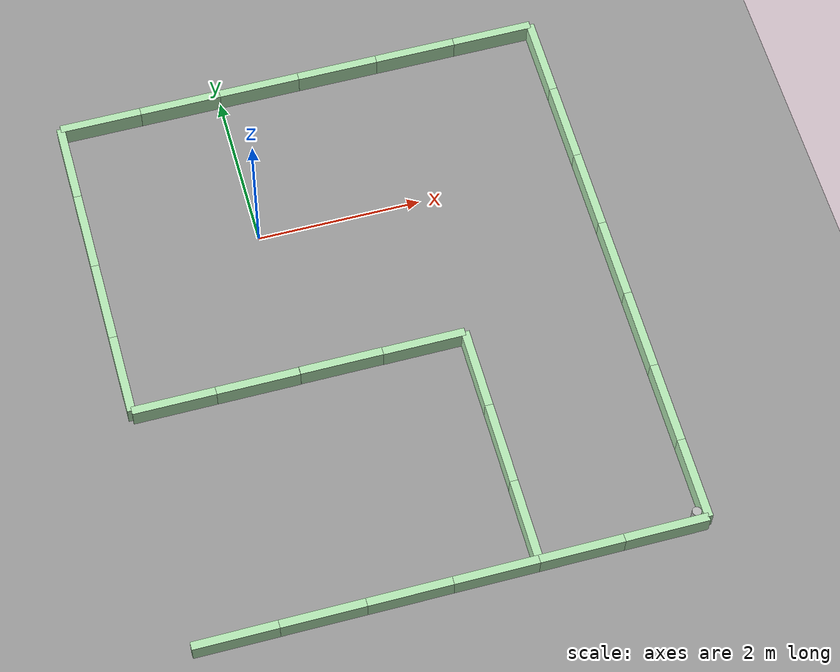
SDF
<sdf version="1.6">
 <world name="default">
  <light name="sun" type="directional">
   <pose>0 0 10 0 -0 0</pose>
   <diffuse>0.8 0.8 0.8 1</diffuse>
   <specular>0.2 0.2 0.2 1</specular>
   <attenuation>
    <range>1000</range>
    <constant>0.9</constant>
    <linear>0.01</linear>
    <quadratic>0.001</quadratic>
   </attenuation>
   <direction>0.5 0.1 -0.9</direction>
  </light>
  <scene><ambient>0.4 0.4 0.4 1</ambient><background>0.7 0.7 0.7 1</background><shadows>1</shadows></scene>
  <physics name="default_physics" default="0" type="ode">
   <max_step_size>0.01</max_step_size>
   <real_time_factor>1</real_time_factor>
   <real_time_update_rate>100</real_time_update_rate>
  </physics>
  <model name="ground_plane_0">
   <static>1</static>
   <link name="link">
    <collision name="collision">
     <geometry><plane><normal>0 0 1</normal><size>100 100</size></plane></geometry>
     <surface><friction><ode><mu>100</mu><mu2>50</mu2></ode></friction></surface>
    </collision>
    <visual name="visual">
     <cast_shadows>0</cast_shadows>
     <geometry><plane><normal>0 0 1</normal><size>100 100</size></plane></geometry>
     <material>
      <script><uri>file://media/materials/scripts/gazebo.material</uri><name>Gazebo/Grey</name></script>
     </material>
    </visual>
    <velocity_decay><linear>0</linear><angular>0</angular></velocity_decay>
   </link>
   <pose>0.497681 0 0 0 -0 0</pose>
  </model>
  <gravity>0 0 -9.8</gravity>
  <magnetic_field>6e-06 2.3e-05 -4.2e-05</magnetic_field>
  <atmosphere type="adiabatic"/>
  <spherical_coordinates>
   <surface_model>EARTH_WGS84</surface_model>
   <latitude_deg>0</latitude_deg>
   <longitude_deg>0</longitude_deg>
   <elevation>0</elevation>
   <heading_deg>0</heading_deg>
  </spherical_coordinates>
  <model name="wall_100_25h">
   <link name="link">
    <inertial>
     <mass>1</mass>
     <inertia>
      <ixx>0.166667</ixx>
      <ixy>0</ixy>
      <ixz>0</ixz>
      <iyy>0.166667</iyy>
      <iyz>0</iyz>
      <izz>0.166667</izz>
     </inertia>
    </inertial>
    <visual name="visual">
     <geometry><box><size>1 0.1 0.25</size></box></geometry>
     <material>
      <script><name>Gazebo/Grey</name><uri>file://media/materials/scripts/gazebo.material</uri></script>
      <ambient>0.3 0.5 0.3 1</ambient>
      <diffuse>0.7 0.9 0.7 1</diffuse>
      <specular>0.01 0.02 0.01 1</specular>
      <emissive>0 0 0 1</emissive>
      <lighting>1</lighting>
      <shader type="vertex"><normal_map>__default__</normal_map></shader>
     </material>
    </visual>
    <collision name="collision">
     <geometry><box><size>1 0.1 0.25</size></box></geometry>
     <surface>
      <friction>
       <ode><mu>1</mu><mu2>1</mu2><fdir1>0 0 0</fdir1><slip1>0</slip1><slip2>0</slip2></ode>
       <torsional>
        <coefficient>1</coefficient>
        <patch_radius>0</patch_radius>
        <surface_radius>0</surface_radius>
        <use_patch_radius>1</use_patch_radius>
        <ode><slip>0</slip></ode>
       </torsional>
      </friction>
      <bounce><restitution_coefficient>0</restitution_coefficient><threshold>1e+06</threshold></bounce>
      <contact>
       <collide_without_contact>0</collide_without_contact>
       <collide_without_contact_bitmask>1</collide_without_contact_bitmask>
       <collide_bitmask>1</collide_bitmask>
       <ode>
        <soft_cfm>0</soft_cfm>
        <soft_erp>0.2</soft_erp>
        <kp>1e+13</kp>
        <kd>1</kd>
        <max_vel>0.01</max_vel>
        <min_depth>0</min_depth>
       </ode>
       <bullet>
        <split_impulse>1</split_impulse>
        <split_impulse_penetration_threshold>-0.01</split_impulse_penetration_threshold>
        <soft_cfm>0</soft_cfm>
        <soft_erp>0.2</soft_erp>
        <kp>1e+13</kp>
        <kd>1</kd>
       </bullet>
      </contact>
     </surface>
    </collision>
   </link>
   <static>1</static>
   <pose>-0.5 2 0.1252 0 -0 0</pose>
  </model>
  <model name="wall_100_25h_clone">
   <link name="link">
    <inertial>
     <mass>1</mass>
     <inertia>
      <ixx>0.166667</ixx>
      <ixy>0</ixy>
      <ixz>0</ixz>
      <iyy>0.166667</iyy>
      <iyz>0</iyz>
      <izz>0.166667</izz>
     </inertia>
    </inertial>
    <visual name="visual">
     <geometry><box><size>1 0.1 0.25</size></box></geometry>
     <material>
      <script><name>Gazebo/Grey</name><uri>file://media/materials/scripts/gazebo.material</uri></script>
      <ambient>0.3 0.5 0.3 1</ambient>
      <diffuse>0.7 0.9 0.7 1</diffuse>
      <specular>0.01 0.02 0.01 1</specular>
      <emissive>0 0 0 1</emissive>
      <lighting>1</lighting>
      <shader type="vertex"><normal_map>__default__</normal_map></shader>
     </material>
    </visual>
    <collision name="collision">
     <geometry><box><size>1 0.1 0.25</size></box></geometry>
     <surface>
      <friction>
       <ode><mu>1</mu><mu2>1</mu2><fdir1>0 0 0</fdir1><slip1>0</slip1><slip2>0</slip2></ode>
       <torsional>
        <coefficient>1</coefficient>
        <patch_radius>0</patch_radius>
        <surface_radius>0</surface_radius>
        <use_patch_radius>1</use_patch_radius>
        <ode><slip>0</slip></ode>
       </torsional>
      </friction>
      <bounce><restitution_coefficient>0</restitution_coefficient><threshold>1e+06</threshold></bounce>
      <contact>
       <collide_without_contact>0</collide_without_contact>
       <collide_without_contact_bitmask>1</collide_without_contact_bitmask>
       <collide_bitmask>1</collide_bitmask>
       <ode>
        <soft_cfm>0</soft_cfm>
        <soft_erp>0.2</soft_erp>
        <kp>1e+13</kp>
        <kd>1</kd>
        <max_vel>0.01</max_vel>
        <min_depth>0</min_depth>
       </ode>
       <bullet>
        <split_impulse>1</split_impulse>
        <split_impulse_penetration_threshold>-0.01</split_impulse_penetration_threshold>
        <soft_cfm>0</soft_cfm>
        <soft_erp>0.2</soft_erp>
        <kp>1e+13</kp>
        <kd>1</kd>
       </bullet>
      </contact>
     </surface>
    </collision>
   </link>
   <static>1</static>
   <pose>0.5 2 0.1252 0 -0 0</pose>
  </model>
  <model name="wall_100_25h_clone_clone">
   <link name="link">
    <inertial>
     <mass>1</mass>
     <inertia>
      <ixx>0.166667</ixx>
      <ixy>0</ixy>
      <ixz>0</ixz>
      <iyy>0.166667</iyy>
      <iyz>0</iyz>
      <izz>0.166667</izz>
     </inertia>
    </inertial>
    <visual name="visual">
     <geometry><box><size>1 0.1 0.25</size></box></geometry>
     <material>
      <script><name>Gazebo/Grey</name><uri>file://media/materials/scripts/gazebo.material</uri></script>
      <ambient>0.3 0.5 0.3 1</ambient>
      <diffuse>0.7 0.9 0.7 1</diffuse>
      <specular>0.01 0.02 0.01 1</specular>
      <emissive>0 0 0 1</emissive>
      <lighting>1</lighting>
      <shader type="vertex"><normal_map>__default__</normal_map></shader>
     </material>
    </visual>
    <collision name="collision">
     <geometry><box><size>1 0.1 0.25</size></box></geometry>
     <surface>
      <friction>
       <ode><mu>1</mu><mu2>1</mu2><fdir1>0 0 0</fdir1><slip1>0</slip1><slip2>0</slip2></ode>
       <torsional>
        <coefficient>1</coefficient>
        <patch_radius>0</patch_radius>
        <surface_radius>0</surface_radius>
        <use_patch_radius>1</use_patch_radius>
        <ode><slip>0</slip></ode>
       </torsional>
      </friction>
      <bounce><restitution_coefficient>0</restitution_coefficient><threshold>1e+06</threshold></bounce>
      <contact>
       <collide_without_contact>0</collide_without_contact>
       <collide_without_contact_bitmask>1</collide_without_contact_bitmask>
       <collide_bitmask>1</collide_bitmask>
       <ode>
        <soft_cfm>0</soft_cfm>
        <soft_erp>0.2</soft_erp>
        <kp>1e+13</kp>
        <kd>1</kd>
        <max_vel>0.01</max_vel>
        <min_depth>0</min_depth>
       </ode>
       <bullet>
        <split_impulse>1</split_impulse>
        <split_impulse_penetration_threshold>-0.01</split_impulse_penetration_threshold>
        <soft_cfm>0</soft_cfm>
        <soft_erp>0.2</soft_erp>
        <kp>1e+13</kp>
        <kd>1</kd>
       </bullet>
      </contact>
     </surface>
    </collision>
   </link>
   <static>1</static>
   <pose>1.5 2 0.1252 0 -0 0</pose>
  </model>
  <model name="wall_100_25h_clone_clone_0">
   <link name="link">
    <inertial>
     <mass>1</mass>
     <inertia>
      <ixx>0.166667</ixx>
      <ixy>0</ixy>
      <ixz>0</ixz>
      <iyy>0.166667</iyy>
      <iyz>0</iyz>
      <izz>0.166667</izz>
     </inertia>
    </inertial>
    <visual name="visual">
     <geometry><box><size>1 0.1 0.25</size></box></geometry>
     <material>
      <script><name>Gazebo/Grey</name><uri>file://media/materials/scripts/gazebo.material</uri></script>
      <ambient>0.3 0.5 0.3 1</ambient>
      <diffuse>0.7 0.9 0.7 1</diffuse>
      <specular>0.01 0.02 0.01 1</specular>
      <emissive>0 0 0 1</emissive>
      <lighting>1</lighting>
      <shader type="vertex"><normal_map>__default__</normal_map></shader>
     </material>
    </visual>
    <collision name="collision">
     <geometry><box><size>1 0.1 0.25</size></box></geometry>
     <surface>
      <friction>
       <ode><mu>1</mu><mu2>1</mu2><fdir1>0 0 0</fdir1><slip1>0</slip1><slip2>0</slip2></ode>
       <torsional>
        <coefficient>1</coefficient>
        <patch_radius>0</patch_radius>
        <surface_radius>0</surface_radius>
        <use_patch_radius>1</use_patch_radius>
        <ode><slip>0</slip></ode>
       </torsional>
      </friction>
      <bounce><restitution_coefficient>0</restitution_coefficient><threshold>1e+06</threshold></bounce>
      <contact>
       <collide_without_contact>0</collide_without_contact>
       <collide_without_contact_bitmask>1</collide_without_contact_bitmask>
       <collide_bitmask>1</collide_bitmask>
       <ode>
        <soft_cfm>0</soft_cfm>
        <soft_erp>0.2</soft_erp>
        <kp>1e+13</kp>
        <kd>1</kd>
        <max_vel>0.01</max_vel>
        <min_depth>0</min_depth>
       </ode>
       <bullet>
        <split_impulse>1</split_impulse>
        <split_impulse_penetration_threshold>-0.01</split_impulse_penetration_threshold>
        <soft_cfm>0</soft_cfm>
        <soft_erp>0.2</soft_erp>
        <kp>1e+13</kp>
        <kd>1</kd>
       </bullet>
      </contact>
     </surface>
    </collision>
   </link>
   <static>1</static>
   <pose>-1.5 2 0.1252 0 -0 0</pose>
  </model>
  <model name="wall_100_25h_clone_clone_1">
   <link name="link">
    <inertial>
     <mass>1</mass>
     <inertia>
      <ixx>0.166667</ixx>
      <ixy>0</ixy>
      <ixz>0</ixz>
      <iyy>0.166667</iyy>
      <iyz>0</iyz>
      <izz>0.166667</izz>
     </inertia>
    </inertial>
    <visual name="visual">
     <geometry><box><size>1 0.1 0.25</size></box></geometry>
     <material>
      <script><name>Gazebo/Grey</name><uri>file://media/materials/scripts/gazebo.material</uri></script>
      <ambient>0.3 0.5 0.3 1</ambient>
      <diffuse>0.7 0.9 0.7 1</diffuse>
      <specular>0.01 0.02 0.01 1</specular>
      <emissive>0 0 0 1</emissive>
      <lighting>1</lighting>
      <shader type="vertex"><normal_map>__default__</normal_map></shader>
     </material>
    </visual>
    <collision name="collision">
     <geometry><box><size>1 0.1 0.25</size></box></geometry>
     <surface>
      <friction>
       <ode><mu>1</mu><mu2>1</mu2><fdir1>0 0 0</fdir1><slip1>0</slip1><slip2>0</slip2></ode>
       <torsional>
        <coefficient>1</coefficient>
        <patch_radius>0</patch_radius>
        <surface_radius>0</surface_radius>
        <use_patch_radius>1</use_patch_radius>
        <ode><slip>0</slip></ode>
       </torsional>
      </friction>
      <bounce><restitution_coefficient>0</restitution_coefficient><threshold>1e+06</threshold></bounce>
      <contact>
       <collide_without_contact>0</collide_without_contact>
       <collide_without_contact_bitmask>1</collide_without_contact_bitmask>
       <collide_bitmask>1</collide_bitmask>
       <ode>
        <soft_cfm>0</soft_cfm>
        <soft_erp>0.2</soft_erp>
        <kp>1e+13</kp>
        <kd>1</kd>
        <max_vel>0.01</max_vel>
        <min_depth>0</min_depth>
       </ode>
       <bullet>
        <split_impulse>1</split_impulse>
        <split_impulse_penetration_threshold>-0.01</split_impulse_penetration_threshold>
        <soft_cfm>0</soft_cfm>
        <soft_erp>0.2</soft_erp>
        <kp>1e+13</kp>
        <kd>1</kd>
       </bullet>
      </contact>
     </surface>
    </collision>
   </link>
   <static>1</static>
   <pose>1.5 -2 0.1252 0 -0 0</pose>
  </model>
  <model name="wall_100_25h_clone_clone_2">
   <link name="link">
    <inertial>
     <mass>1</mass>
     <inertia>
      <ixx>0.166667</ixx>
      <ixy>0</ixy>
      <ixz>0</ixz>
      <iyy>0.166667</iyy>
      <iyz>0</iyz>
      <izz>0.166667</izz>
     </inertia>
    </inertial>
    <visual name="visual">
     <geometry><box><size>1 0.1 0.25</size></box></geometry>
     <material>
      <script><name>Gazebo/Grey</name><uri>file://media/materials/scripts/gazebo.material</uri></script>
      <ambient>0.3 0.5 0.3 1</ambient>
      <diffuse>0.7 0.9 0.7 1</diffuse>
      <specular>0.01 0.02 0.01 1</specular>
      <emissive>0 0 0 1</emissive>
      <lighting>1</lighting>
      <shader type="vertex"><normal_map>__default__</normal_map></shader>
     </material>
    </visual>
    <collision name="collision">
     <geometry><box><size>1 0.1 0.25</size></box></geometry>
     <surface>
      <friction>
       <ode><mu>1</mu><mu2>1</mu2><fdir1>0 0 0</fdir1><slip1>0</slip1><slip2>0</slip2></ode>
       <torsional>
        <coefficient>1</coefficient>
        <patch_radius>0</patch_radius>
        <surface_radius>0</surface_radius>
        <use_patch_radius>1</use_patch_radius>
        <ode><slip>0</slip></ode>
       </torsional>
      </friction>
      <bounce><restitution_coefficient>0</restitution_coefficient><threshold>1e+06</threshold></bounce>
      <contact>
       <collide_without_contact>0</collide_without_contact>
       <collide_without_contact_bitmask>1</collide_without_contact_bitmask>
       <collide_bitmask>1</collide_bitmask>
       <ode>
        <soft_cfm>0</soft_cfm>
        <soft_erp>0.2</soft_erp>
        <kp>1e+13</kp>
        <kd>1</kd>
        <max_vel>0.01</max_vel>
        <min_depth>0</min_depth>
       </ode>
       <bullet>
        <split_impulse>1</split_impulse>
        <split_impulse_penetration_threshold>-0.01</split_impulse_penetration_threshold>
        <soft_cfm>0</soft_cfm>
        <soft_erp>0.2</soft_erp>
        <kp>1e+13</kp>
        <kd>1</kd>
       </bullet>
      </contact>
     </surface>
    </collision>
   </link>
   <static>1</static>
   <pose>0.502276 -1.99731 0.1252 0 -0 0</pose>
  </model>
  <model name="wall_100_25h_clone_clone_3">
   <link name="link">
    <inertial>
     <mass>1</mass>
     <inertia>
      <ixx>0.166667</ixx>
      <ixy>0</ixy>
      <ixz>0</ixz>
      <iyy>0.166667</iyy>
      <iyz>0</iyz>
      <izz>0.166667</izz>
     </inertia>
    </inertial>
    <visual name="visual">
     <geometry><box><size>1 0.1 0.25</size></box></geometry>
     <material>
      <script><name>Gazebo/Grey</name><uri>file://media/materials/scripts/gazebo.material</uri></script>
      <ambient>0.3 0.5 0.3 1</ambient>
      <diffuse>0.7 0.9 0.7 1</diffuse>
      <specular>0.01 0.02 0.01 1</specular>
      <emissive>0 0 0 1</emissive>
      <lighting>1</lighting>
      <shader type="vertex"><normal_map>__default__</normal_map></shader>
     </material>
    </visual>
    <collision name="collision">
     <geometry><box><size>1 0.1 0.25</size></box></geometry>
     <surface>
      <friction>
       <ode><mu>1</mu><mu2>1</mu2><fdir1>0 0 0</fdir1><slip1>0</slip1><slip2>0</slip2></ode>
       <torsional>
        <coefficient>1</coefficient>
        <patch_radius>0</patch_radius>
        <surface_radius>0</surface_radius>
        <use_patch_radius>1</use_patch_radius>
        <ode><slip>0</slip></ode>
       </torsional>
      </friction>
      <bounce><restitution_coefficient>0</restitution_coefficient><threshold>1e+06</threshold></bounce>
      <contact>
       <collide_without_contact>0</collide_without_contact>
       <collide_without_contact_bitmask>1</collide_without_contact_bitmask>
       <collide_bitmask>1</collide_bitmask>
       <ode>
        <soft_cfm>0</soft_cfm>
        <soft_erp>0.2</soft_erp>
        <kp>1e+13</kp>
        <kd>1</kd>
        <max_vel>0.01</max_vel>
        <min_depth>0</min_depth>
       </ode>
       <bullet>
        <split_impulse>1</split_impulse>
        <split_impulse_penetration_threshold>-0.01</split_impulse_penetration_threshold>
        <soft_cfm>0</soft_cfm>
        <soft_erp>0.2</soft_erp>
        <kp>1e+13</kp>
        <kd>1</kd>
       </bullet>
      </contact>
     </surface>
    </collision>
   </link>
   <static>1</static>
   <pose>-0.501577 -2 0.1252 0 -0 0</pose>
  </model>
  <model name="wall_100_25h_clone_clone_4">
   <link name="link">
    <inertial>
     <mass>1</mass>
     <inertia>
      <ixx>0.166667</ixx>
      <ixy>0</ixy>
      <ixz>0</ixz>
      <iyy>0.166667</iyy>
      <iyz>0</iyz>
      <izz>0.166667</izz>
     </inertia>
    </inertial>
    <visual name="visual">
     <geometry><box><size>1 0.1 0.25</size></box></geometry>
     <material>
      <script><name>Gazebo/Grey</name><uri>file://media/materials/scripts/gazebo.material</uri></script>
      <ambient>0.3 0.5 0.3 1</ambient>
      <diffuse>0.7 0.9 0.7 1</diffuse>
      <specular>0.01 0.02 0.01 1</specular>
      <emissive>0 0 0 1</emissive>
      <lighting>1</lighting>
      <shader type="vertex"><normal_map>__default__</normal_map></shader>
     </material>
    </visual>
    <collision name="collision">
     <geometry><box><size>1 0.1 0.25</size></box></geometry>
     <surface>
      <friction>
       <ode><mu>1</mu><mu2>1</mu2><fdir1>0 0 0</fdir1><slip1>0</slip1><slip2>0</slip2></ode>
       <torsional>
        <coefficient>1</coefficient>
        <patch_radius>0</patch_radius>
        <surface_radius>0</surface_radius>
        <use_patch_radius>1</use_patch_radius>
        <ode><slip>0</slip></ode>
       </torsional>
      </friction>
      <bounce><restitution_coefficient>0</restitution_coefficient><threshold>1e+06</threshold></bounce>
      <contact>
       <collide_without_contact>0</collide_without_contact>
       <collide_without_contact_bitmask>1</collide_without_contact_bitmask>
       <collide_bitmask>1</collide_bitmask>
       <ode>
        <soft_cfm>0</soft_cfm>
        <soft_erp>0.2</soft_erp>
        <kp>1e+13</kp>
        <kd>1</kd>
        <max_vel>0.01</max_vel>
        <min_depth>0</min_depth>
       </ode>
       <bullet>
        <split_impulse>1</split_impulse>
        <split_impulse_penetration_threshold>-0.01</split_impulse_penetration_threshold>
        <soft_cfm>0</soft_cfm>
        <soft_erp>0.2</soft_erp>
        <kp>1e+13</kp>
        <kd>1</kd>
       </bullet>
      </contact>
     </surface>
    </collision>
   </link>
   <static>1</static>
   <pose>-1.5 -2 0.1252 0 -0 0</pose>
  </model>
  <model name="wall_100_25h_clone_clone_5_clone_1">
   <link name="link">
    <inertial>
     <mass>1</mass>
     <inertia>
      <ixx>0.166667</ixx>
      <ixy>0</ixy>
      <ixz>0</ixz>
      <iyy>0.166667</iyy>
      <iyz>0</iyz>
      <izz>0.166667</izz>
     </inertia>
    </inertial>
    <visual name="visual">
     <geometry><box><size>1 0.1 0.25</size></box></geometry>
     <material>
      <script><name>Gazebo/Grey</name><uri>file://media/materials/scripts/gazebo.material</uri></script>
      <ambient>0.3 0.5 0.3 1</ambient>
      <diffuse>0.7 0.9 0.7 1</diffuse>
      <specular>0.01 0.02 0.01 1</specular>
      <emissive>0 0 0 1</emissive>
      <lighting>1</lighting>
      <shader type="vertex"><normal_map>__default__</normal_map></shader>
     </material>
    </visual>
    <collision name="collision">
     <geometry><box><size>1 0.1 0.25</size></box></geometry>
     <surface>
      <friction>
       <ode><mu>1</mu><mu2>1</mu2><fdir1>0 0 0</fdir1><slip1>0</slip1><slip2>0</slip2></ode>
       <torsional>
        <coefficient>1</coefficient>
        <patch_radius>0</patch_radius>
        <surface_radius>0</surface_radius>
        <use_patch_radius>1</use_patch_radius>
        <ode><slip>0</slip></ode>
       </torsional>
      </friction>
      <bounce><restitution_coefficient>0</restitution_coefficient><threshold>1e+06</threshold></bounce>
      <contact>
       <collide_without_contact>0</collide_without_contact>
       <collide_without_contact_bitmask>1</collide_without_contact_bitmask>
       <collide_bitmask>1</collide_bitmask>
       <ode>
        <soft_cfm>0</soft_cfm>
        <soft_erp>0.2</soft_erp>
        <kp>1e+13</kp>
        <kd>1</kd>
        <max_vel>0.01</max_vel>
        <min_depth>0</min_depth>
       </ode>
       <bullet>
        <split_impulse>1</split_impulse>
        <split_impulse_penetration_threshold>-0.01</split_impulse_penetration_threshold>
        <soft_cfm>0</soft_cfm>
        <soft_erp>0.2</soft_erp>
        <kp>1e+13</kp>
        <kd>1</kd>
       </bullet>
      </contact>
     </surface>
    </collision>
   </link>
   <static>1</static>
   <pose>4 -2.5 0.1252 0 0 -1.5708</pose>
  </model>
  <model name="wall_100_25h_clone_clone_5_clone_2">
   <link name="link">
    <inertial>
     <mass>1</mass>
     <inertia>
      <ixx>0.166667</ixx>
      <ixy>0</ixy>
      <ixz>0</ixz>
      <iyy>0.166667</iyy>
      <iyz>0</iyz>
      <izz>0.166667</izz>
     </inertia>
    </inertial>
    <visual name="visual">
     <geometry><box><size>1 0.1 0.25</size></box></geometry>
     <material>
      <script><name>Gazebo/Grey</name><uri>file://media/materials/scripts/gazebo.material</uri></script>
      <ambient>0.3 0.5 0.3 1</ambient>
      <diffuse>0.7 0.9 0.7 1</diffuse>
      <specular>0.01 0.02 0.01 1</specular>
      <emissive>0 0 0 1</emissive>
      <lighting>1</lighting>
      <shader type="vertex"><normal_map>__default__</normal_map></shader>
     </material>
    </visual>
    <collision name="collision">
     <geometry><box><size>1 0.1 0.25</size></box></geometry>
     <surface>
      <friction>
       <ode><mu>1</mu><mu2>1</mu2><fdir1>0 0 0</fdir1><slip1>0</slip1><slip2>0</slip2></ode>
       <torsional>
        <coefficient>1</coefficient>
        <patch_radius>0</patch_radius>
        <surface_radius>0</surface_radius>
        <use_patch_radius>1</use_patch_radius>
        <ode><slip>0</slip></ode>
       </torsional>
      </friction>
      <bounce><restitution_coefficient>0</restitution_coefficient><threshold>1e+06</threshold></bounce>
      <contact>
       <collide_without_contact>0</collide_without_contact>
       <collide_without_contact_bitmask>1</collide_without_contact_bitmask>
       <collide_bitmask>1</collide_bitmask>
       <ode>
        <soft_cfm>0</soft_cfm>
        <soft_erp>0.2</soft_erp>
        <kp>1e+13</kp>
        <kd>1</kd>
        <max_vel>0.01</max_vel>
        <min_depth>0</min_depth>
       </ode>
       <bullet>
        <split_impulse>1</split_impulse>
        <split_impulse_penetration_threshold>-0.01</split_impulse_penetration_threshold>
        <soft_cfm>0</soft_cfm>
        <soft_erp>0.2</soft_erp>
        <kp>1e+13</kp>
        <kd>1</kd>
       </bullet>
      </contact>
     </surface>
    </collision>
   </link>
   <static>1</static>
   <pose>-2 -1.5 0.1252 0 0 -1.57</pose>
  </model>
  <model name="wall_100_25h_clone_clone_5_clone_3">
   <link name="link">
    <inertial>
     <mass>1</mass>
     <inertia>
      <ixx>0.166667</ixx>
      <ixy>0</ixy>
      <ixz>0</ixz>
      <iyy>0.166667</iyy>
      <iyz>0</iyz>
      <izz>0.166667</izz>
     </inertia>
    </inertial>
    <visual name="visual">
     <geometry><box><size>1 0.1 0.25</size></box></geometry>
     <material>
      <script><name>Gazebo/Grey</name><uri>file://media/materials/scripts/gazebo.material</uri></script>
      <ambient>0.3 0.5 0.3 1</ambient>
      <diffuse>0.7 0.9 0.7 1</diffuse>
      <specular>0.01 0.02 0.01 1</specular>
      <emissive>0 0 0 1</emissive>
      <lighting>1</lighting>
      <shader type="vertex"><normal_map>__default__</normal_map></shader>
     </material>
    </visual>
    <collision name="collision">
     <geometry><box><size>1 0.1 0.25</size></box></geometry>
     <surface>
      <friction>
       <ode><mu>1</mu><mu2>1</mu2><fdir1>0 0 0</fdir1><slip1>0</slip1><slip2>0</slip2></ode>
       <torsional>
        <coefficient>1</coefficient>
        <patch_radius>0</patch_radius>
        <surface_radius>0</surface_radius>
        <use_patch_radius>1</use_patch_radius>
        <ode><slip>0</slip></ode>
       </torsional>
      </friction>
      <bounce><restitution_coefficient>0</restitution_coefficient><threshold>1e+06</threshold></bounce>
      <contact>
       <collide_without_contact>0</collide_without_contact>
       <collide_without_contact_bitmask>1</collide_without_contact_bitmask>
       <collide_bitmask>1</collide_bitmask>
       <ode>
        <soft_cfm>0</soft_cfm>
        <soft_erp>0.2</soft_erp>
        <kp>1e+13</kp>
        <kd>1</kd>
        <max_vel>0.01</max_vel>
        <min_depth>0</min_depth>
       </ode>
       <bullet>
        <split_impulse>1</split_impulse>
        <split_impulse_penetration_threshold>-0.01</split_impulse_penetration_threshold>
        <soft_cfm>0</soft_cfm>
        <soft_erp>0.2</soft_erp>
        <kp>1e+13</kp>
        <kd>1</kd>
       </bullet>
      </contact>
     </surface>
    </collision>
   </link>
   <static>1</static>
   <pose>-2 -0.5 0.1252 0 0 -1.57</pose>
  </model>
  <model name="wall_100_25h_clone_clone_5_clone_4">
   <link name="link">
    <inertial>
     <mass>1</mass>
     <inertia>
      <ixx>0.166667</ixx>
      <ixy>0</ixy>
      <ixz>0</ixz>
      <iyy>0.166667</iyy>
      <iyz>0</iyz>
      <izz>0.166667</izz>
     </inertia>
    </inertial>
    <visual name="visual">
     <geometry><box><size>1 0.1 0.25</size></box></geometry>
     <material>
      <script><name>Gazebo/Grey</name><uri>file://media/materials/scripts/gazebo.material</uri></script>
      <ambient>0.3 0.5 0.3 1</ambient>
      <diffuse>0.7 0.9 0.7 1</diffuse>
      <specular>0.01 0.02 0.01 1</specular>
      <emissive>0 0 0 1</emissive>
      <lighting>1</lighting>
      <shader type="vertex"><normal_map>__default__</normal_map></shader>
     </material>
    </visual>
    <collision name="collision">
     <geometry><box><size>1 0.1 0.25</size></box></geometry>
     <surface>
      <friction>
       <ode><mu>1</mu><mu2>1</mu2><fdir1>0 0 0</fdir1><slip1>0</slip1><slip2>0</slip2></ode>
       <torsional>
        <coefficient>1</coefficient>
        <patch_radius>0</patch_radius>
        <surface_radius>0</surface_radius>
        <use_patch_radius>1</use_patch_radius>
        <ode><slip>0</slip></ode>
       </torsional>
      </friction>
      <bounce><restitution_coefficient>0</restitution_coefficient><threshold>1e+06</threshold></bounce>
      <contact>
       <collide_without_contact>0</collide_without_contact>
       <collide_without_contact_bitmask>1</collide_without_contact_bitmask>
       <collide_bitmask>1</collide_bitmask>
       <ode>
        <soft_cfm>0</soft_cfm>
        <soft_erp>0.2</soft_erp>
        <kp>1e+13</kp>
        <kd>1</kd>
        <max_vel>0.01</max_vel>
        <min_depth>0</min_depth>
       </ode>
       <bullet>
        <split_impulse>1</split_impulse>
        <split_impulse_penetration_threshold>-0.01</split_impulse_penetration_threshold>
        <soft_cfm>0</soft_cfm>
        <soft_erp>0.2</soft_erp>
        <kp>1e+13</kp>
        <kd>1</kd>
       </bullet>
      </contact>
     </surface>
    </collision>
   </link>
   <static>1</static>
   <pose>-2 0.5 0.1252 0 0 -1.57</pose>
  </model>
  <model name="wall_100_25h_clone_clone_5_clone_5">
   <link name="link">
    <inertial>
     <mass>1</mass>
     <inertia>
      <ixx>0.166667</ixx>
      <ixy>0</ixy>
      <ixz>0</ixz>
      <iyy>0.166667</iyy>
      <iyz>0</iyz>
      <izz>0.166667</izz>
     </inertia>
    </inertial>
    <visual name="visual">
     <geometry><box><size>1 0.1 0.25</size></box></geometry>
     <material>
      <script><name>Gazebo/Grey</name><uri>file://media/materials/scripts/gazebo.material</uri></script>
      <ambient>0.3 0.5 0.3 1</ambient>
      <diffuse>0.7 0.9 0.7 1</diffuse>
      <specular>0.01 0.02 0.01 1</specular>
      <emissive>0 0 0 1</emissive>
      <lighting>1</lighting>
      <shader type="vertex"><normal_map>__default__</normal_map></shader>
     </material>
    </visual>
    <collision name="collision">
     <geometry><box><size>1 0.1 0.25</size></box></geometry>
     <surface>
      <friction>
       <ode><mu>1</mu><mu2>1</mu2><fdir1>0 0 0</fdir1><slip1>0</slip1><slip2>0</slip2></ode>
       <torsional>
        <coefficient>1</coefficient>
        <patch_radius>0</patch_radius>
        <surface_radius>0</surface_radius>
        <use_patch_radius>1</use_patch_radius>
        <ode><slip>0</slip></ode>
       </torsional>
      </friction>
      <bounce><restitution_coefficient>0</restitution_coefficient><threshold>1e+06</threshold></bounce>
      <contact>
       <collide_without_contact>0</collide_without_contact>
       <collide_without_contact_bitmask>1</collide_without_contact_bitmask>
       <collide_bitmask>1</collide_bitmask>
       <ode>
        <soft_cfm>0</soft_cfm>
        <soft_erp>0.2</soft_erp>
        <kp>1e+13</kp>
        <kd>1</kd>
        <max_vel>0.01</max_vel>
        <min_depth>0</min_depth>
       </ode>
       <bullet>
        <split_impulse>1</split_impulse>
        <split_impulse_penetration_threshold>-0.01</split_impulse_penetration_threshold>
        <soft_cfm>0</soft_cfm>
        <soft_erp>0.2</soft_erp>
        <kp>1e+13</kp>
        <kd>1</kd>
       </bullet>
      </contact>
     </surface>
    </collision>
   </link>
   <static>1</static>
   <pose>-2 1.5 0.1252 0 0 -1.57</pose>
  </model>
  <model name="wall_100_25h_clone_clone_5_clone_1_clone">
   <link name="link">
    <inertial>
     <mass>1</mass>
     <inertia>
      <ixx>0.166667</ixx>
      <ixy>0</ixy>
      <ixz>0</ixz>
      <iyy>0.166667</iyy>
      <iyz>0</iyz>
      <izz>0.166667</izz>
     </inertia>
    </inertial>
    <visual name="visual">
     <geometry><box><size>1 0.1 0.25</size></box></geometry>
     <material>
      <script><name>Gazebo/Grey</name><uri>file://media/materials/scripts/gazebo.material</uri></script>
      <ambient>0.3 0.5 0.3 1</ambient>
      <diffuse>0.7 0.9 0.7 1</diffuse>
      <specular>0.01 0.02 0.01 1</specular>
      <emissive>0 0 0 1</emissive>
      <lighting>1</lighting>
      <shader type="vertex"><normal_map>__default__</normal_map></shader>
     </material>
    </visual>
    <collision name="collision">
     <geometry><box><size>1 0.1 0.25</size></box></geometry>
     <surface>
      <friction>
       <ode><mu>1</mu><mu2>1</mu2><fdir1>0 0 0</fdir1><slip1>0</slip1><slip2>0</slip2></ode>
       <torsional>
        <coefficient>1</coefficient>
        <patch_radius>0</patch_radius>
        <surface_radius>0</surface_radius>
        <use_patch_radius>1</use_patch_radius>
        <ode><slip>0</slip></ode>
       </torsional>
      </friction>
      <bounce><restitution_coefficient>0</restitution_coefficient><threshold>1e+06</threshold></bounce>
      <contact>
       <collide_without_contact>0</collide_without_contact>
       <collide_without_contact_bitmask>1</collide_without_contact_bitmask>
       <collide_bitmask>1</collide_bitmask>
       <ode>
        <soft_cfm>0</soft_cfm>
        <soft_erp>0.2</soft_erp>
        <kp>1e+13</kp>
        <kd>1</kd>
        <max_vel>0.01</max_vel>
        <min_depth>0</min_depth>
       </ode>
       <bullet>
        <split_impulse>1</split_impulse>
        <split_impulse_penetration_threshold>-0.01</split_impulse_penetration_threshold>
        <soft_cfm>0</soft_cfm>
        <soft_erp>0.2</soft_erp>
        <kp>1e+13</kp>
        <kd>1</kd>
       </bullet>
      </contact>
     </surface>
    </collision>
   </link>
   <static>1</static>
   <pose>4 -3.5 0.1252 0 0 -1.5708</pose>
  </model>
  <model name="wall_100_25h_clone_clone_5_clone_1_clone_0">
   <link name="link">
    <inertial>
     <mass>1</mass>
     <inertia>
      <ixx>0.166667</ixx>
      <ixy>0</ixy>
      <ixz>0</ixz>
      <iyy>0.166667</iyy>
      <iyz>0</iyz>
      <izz>0.166667</izz>
     </inertia>
    </inertial>
    <visual name="visual">
     <geometry><box><size>1 0.1 0.25</size></box></geometry>
     <material>
      <script><name>Gazebo/Grey</name><uri>file://media/materials/scripts/gazebo.material</uri></script>
      <ambient>0.3 0.5 0.3 1</ambient>
      <diffuse>0.7 0.9 0.7 1</diffuse>
      <specular>0.01 0.02 0.01 1</specular>
      <emissive>0 0 0 1</emissive>
      <lighting>1</lighting>
      <shader type="vertex"><normal_map>__default__</normal_map></shader>
     </material>
    </visual>
    <collision name="collision">
     <geometry><box><size>1 0.1 0.25</size></box></geometry>
     <surface>
      <friction>
       <ode><mu>1</mu><mu2>1</mu2><fdir1>0 0 0</fdir1><slip1>0</slip1><slip2>0</slip2></ode>
       <torsional>
        <coefficient>1</coefficient>
        <patch_radius>0</patch_radius>
        <surface_radius>0</surface_radius>
        <use_patch_radius>1</use_patch_radius>
        <ode><slip>0</slip></ode>
       </torsional>
      </friction>
      <bounce><restitution_coefficient>0</restitution_coefficient><threshold>1e+06</threshold></bounce>
      <contact>
       <collide_without_contact>0</collide_without_contact>
       <collide_without_contact_bitmask>1</collide_without_contact_bitmask>
       <collide_bitmask>1</collide_bitmask>
       <ode>
        <soft_cfm>0</soft_cfm>
        <soft_erp>0.2</soft_erp>
        <kp>1e+13</kp>
        <kd>1</kd>
        <max_vel>0.01</max_vel>
        <min_depth>0</min_depth>
       </ode>
       <bullet>
        <split_impulse>1</split_impulse>
        <split_impulse_penetration_threshold>-0.01</split_impulse_penetration_threshold>
        <soft_cfm>0</soft_cfm>
        <soft_erp>0.2</soft_erp>
        <kp>1e+13</kp>
        <kd>1</kd>
       </bullet>
      </contact>
     </surface>
    </collision>
   </link>
   <static>1</static>
   <pose>4 -4.5 0.1252 0 0 -1.5708</pose>
  </model>
  <model name="wall_100_25h_clone_clone_5_clone_1_clone_1">
   <link name="link">
    <inertial>
     <mass>1</mass>
     <inertia>
      <ixx>0.166667</ixx>
      <ixy>0</ixy>
      <ixz>0</ixz>
      <iyy>0.166667</iyy>
      <iyz>0</iyz>
      <izz>0.166667</izz>
     </inertia>
    </inertial>
    <visual name="visual">
     <geometry><box><size>1 0.1 0.25</size></box></geometry>
     <material>
      <script><name>Gazebo/Grey</name><uri>file://media/materials/scripts/gazebo.material</uri></script>
      <ambient>0.3 0.5 0.3 1</ambient>
      <diffuse>0.7 0.9 0.7 1</diffuse>
      <specular>0.01 0.02 0.01 1</specular>
      <emissive>0 0 0 1</emissive>
      <lighting>1</lighting>
      <shader type="vertex"><normal_map>__default__</normal_map></shader>
     </material>
    </visual>
    <collision name="collision">
     <geometry><box><size>1 0.1 0.25</size></box></geometry>
     <surface>
      <friction>
       <ode><mu>1</mu><mu2>1</mu2><fdir1>0 0 0</fdir1><slip1>0</slip1><slip2>0</slip2></ode>
       <torsional>
        <coefficient>1</coefficient>
        <patch_radius>0</patch_radius>
        <surface_radius>0</surface_radius>
        <use_patch_radius>1</use_patch_radius>
        <ode><slip>0</slip></ode>
       </torsional>
      </friction>
      <bounce><restitution_coefficient>0</restitution_coefficient><threshold>1e+06</threshold></bounce>
      <contact>
       <collide_without_contact>0</collide_without_contact>
       <collide_without_contact_bitmask>1</collide_without_contact_bitmask>
       <collide_bitmask>1</collide_bitmask>
       <ode>
        <soft_cfm>0</soft_cfm>
        <soft_erp>0.2</soft_erp>
        <kp>1e+13</kp>
        <kd>1</kd>
        <max_vel>0.01</max_vel>
        <min_depth>0</min_depth>
       </ode>
       <bullet>
        <split_impulse>1</split_impulse>
        <split_impulse_penetration_threshold>-0.01</split_impulse_penetration_threshold>
        <soft_cfm>0</soft_cfm>
        <soft_erp>0.2</soft_erp>
        <kp>1e+13</kp>
        <kd>1</kd>
       </bullet>
      </contact>
     </surface>
    </collision>
   </link>
   <static>1</static>
   <pose>4 -1.5 0.1252 0 0 -1.5708</pose>
  </model>
  <model name="wall_100_25h_clone_clone_5_clone_1_clone_2">
   <link name="link">
    <inertial>
     <mass>1</mass>
     <inertia>
      <ixx>0.166667</ixx>
      <ixy>0</ixy>
      <ixz>0</ixz>
      <iyy>0.166667</iyy>
      <iyz>0</iyz>
      <izz>0.166667</izz>
     </inertia>
    </inertial>
    <visual name="visual">
     <geometry><box><size>1 0.1 0.25</size></box></geometry>
     <material>
      <script><name>Gazebo/Grey</name><uri>file://media/materials/scripts/gazebo.material</uri></script>
      <ambient>0.3 0.5 0.3 1</ambient>
      <diffuse>0.7 0.9 0.7 1</diffuse>
      <specular>0.01 0.02 0.01 1</specular>
      <emissive>0 0 0 1</emissive>
      <lighting>1</lighting>
      <shader type="vertex"><normal_map>__default__</normal_map></shader>
     </material>
    </visual>
    <collision name="collision">
     <geometry><box><size>1 0.1 0.25</size></box></geometry>
     <surface>
      <friction>
       <ode><mu>1</mu><mu2>1</mu2><fdir1>0 0 0</fdir1><slip1>0</slip1><slip2>0</slip2></ode>
       <torsional>
        <coefficient>1</coefficient>
        <patch_radius>0</patch_radius>
        <surface_radius>0</surface_radius>
        <use_patch_radius>1</use_patch_radius>
        <ode><slip>0</slip></ode>
       </torsional>
      </friction>
      <bounce><restitution_coefficient>0</restitution_coefficient><threshold>1e+06</threshold></bounce>
      <contact>
       <collide_without_contact>0</collide_without_contact>
       <collide_without_contact_bitmask>1</collide_without_contact_bitmask>
       <collide_bitmask>1</collide_bitmask>
       <ode>
        <soft_cfm>0</soft_cfm>
        <soft_erp>0.2</soft_erp>
        <kp>1e+13</kp>
        <kd>1</kd>
        <max_vel>0.01</max_vel>
        <min_depth>0</min_depth>
       </ode>
       <bullet>
        <split_impulse>1</split_impulse>
        <split_impulse_penetration_threshold>-0.01</split_impulse_penetration_threshold>
        <soft_cfm>0</soft_cfm>
        <soft_erp>0.2</soft_erp>
        <kp>1e+13</kp>
        <kd>1</kd>
       </bullet>
      </contact>
     </surface>
    </collision>
   </link>
   <static>1</static>
   <pose>4 -0.5 0.1252 0 0 -1.5708</pose>
  </model>
  <model name="wall_100_25h_clone_clone_5_clone_1_clone_3">
   <link name="link">
    <inertial>
     <mass>1</mass>
     <inertia>
      <ixx>0.166667</ixx>
      <ixy>0</ixy>
      <ixz>0</ixz>
      <iyy>0.166667</iyy>
      <iyz>0</iyz>
      <izz>0.166667</izz>
     </inertia>
    </inertial>
    <visual name="visual">
     <geometry><box><size>1 0.1 0.25</size></box></geometry>
     <material>
      <script><name>Gazebo/Grey</name><uri>file://media/materials/scripts/gazebo.material</uri></script>
      <ambient>0.3 0.5 0.3 1</ambient>
      <diffuse>0.7 0.9 0.7 1</diffuse>
      <specular>0.01 0.02 0.01 1</specular>
      <emissive>0 0 0 1</emissive>
      <lighting>1</lighting>
      <shader type="vertex"><normal_map>__default__</normal_map></shader>
     </material>
    </visual>
    <collision name="collision">
     <geometry><box><size>1 0.1 0.25</size></box></geometry>
     <surface>
      <friction>
       <ode><mu>1</mu><mu2>1</mu2><fdir1>0 0 0</fdir1><slip1>0</slip1><slip2>0</slip2></ode>
       <torsional>
        <coefficient>1</coefficient>
        <patch_radius>0</patch_radius>
        <surface_radius>0</surface_radius>
        <use_patch_radius>1</use_patch_radius>
        <ode><slip>0</slip></ode>
       </torsional>
      </friction>
      <bounce><restitution_coefficient>0</restitution_coefficient><threshold>1e+06</threshold></bounce>
      <contact>
       <collide_without_contact>0</collide_without_contact>
       <collide_without_contact_bitmask>1</collide_without_contact_bitmask>
       <collide_bitmask>1</collide_bitmask>
       <ode>
        <soft_cfm>0</soft_cfm>
        <soft_erp>0.2</soft_erp>
        <kp>1e+13</kp>
        <kd>1</kd>
        <max_vel>0.01</max_vel>
        <min_depth>0</min_depth>
       </ode>
       <bullet>
        <split_impulse>1</split_impulse>
        <split_impulse_penetration_threshold>-0.01</split_impulse_penetration_threshold>
        <soft_cfm>0</soft_cfm>
        <soft_erp>0.2</soft_erp>
        <kp>1e+13</kp>
        <kd>1</kd>
       </bullet>
      </contact>
     </surface>
    </collision>
   </link>
   <static>1</static>
   <pose>4 0.5 0.1252 0 0 -1.5708</pose>
  </model>
  <model name="wall_100_25h_clone_clone_5_clone_1_clone_4">
   <link name="link">
    <inertial>
     <mass>1</mass>
     <inertia>
      <ixx>0.166667</ixx>
      <ixy>0</ixy>
      <ixz>0</ixz>
      <iyy>0.166667</iyy>
      <iyz>0</iyz>
      <izz>0.166667</izz>
     </inertia>
    </inertial>
    <visual name="visual">
     <geometry><box><size>1 0.1 0.25</size></box></geometry>
     <material>
      <script><name>Gazebo/Grey</name><uri>file://media/materials/scripts/gazebo.material</uri></script>
      <ambient>0.3 0.5 0.3 1</ambient>
      <diffuse>0.7 0.9 0.7 1</diffuse>
      <specular>0.01 0.02 0.01 1</specular>
      <emissive>0 0 0 1</emissive>
      <lighting>1</lighting>
      <shader type="vertex"><normal_map>__default__</normal_map></shader>
     </material>
    </visual>
    <collision name="collision">
     <geometry><box><size>1 0.1 0.25</size></box></geometry>
     <surface>
      <friction>
       <ode><mu>1</mu><mu2>1</mu2><fdir1>0 0 0</fdir1><slip1>0</slip1><slip2>0</slip2></ode>
       <torsional>
        <coefficient>1</coefficient>
        <patch_radius>0</patch_radius>
        <surface_radius>0</surface_radius>
        <use_patch_radius>1</use_patch_radius>
        <ode><slip>0</slip></ode>
       </torsional>
      </friction>
      <bounce><restitution_coefficient>0</restitution_coefficient><threshold>1e+06</threshold></bounce>
      <contact>
       <collide_without_contact>0</collide_without_contact>
       <collide_without_contact_bitmask>1</collide_without_contact_bitmask>
       <collide_bitmask>1</collide_bitmask>
       <ode>
        <soft_cfm>0</soft_cfm>
        <soft_erp>0.2</soft_erp>
        <kp>1e+13</kp>
        <kd>1</kd>
        <max_vel>0.01</max_vel>
        <min_depth>0</min_depth>
       </ode>
       <bullet>
        <split_impulse>1</split_impulse>
        <split_impulse_penetration_threshold>-0.01</split_impulse_penetration_threshold>
        <soft_cfm>0</soft_cfm>
        <soft_erp>0.2</soft_erp>
        <kp>1e+13</kp>
        <kd>1</kd>
       </bullet>
      </contact>
     </surface>
    </collision>
   </link>
   <static>1</static>
   <pose>4 1.5 0.1252 0 0 -1.5708</pose>
  </model>
  <model name="wall_100_25h_clone_clone_1_clone">
   <link name="link">
    <inertial>
     <mass>1</mass>
     <inertia>
      <ixx>0.166667</ixx>
      <ixy>0</ixy>
      <ixz>0</ixz>
      <iyy>0.166667</iyy>
      <iyz>0</iyz>
      <izz>0.166667</izz>
     </inertia>
    </inertial>
    <visual name="visual">
     <geometry><box><size>1 0.1 0.25</size></box></geometry>
     <material>
      <script><name>Gazebo/Grey</name><uri>file://media/materials/scripts/gazebo.material</uri></script>
      <ambient>0.3 0.5 0.3 1</ambient>
      <diffuse>0.7 0.9 0.7 1</diffuse>
      <specular>0.01 0.02 0.01 1</specular>
      <emissive>0 0 0 1</emissive>
      <lighting>1</lighting>
      <shader type="vertex"><normal_map>__default__</normal_map></shader>
     </material>
    </visual>
    <collision name="collision">
     <geometry><box><size>1 0.1 0.25</size></box></geometry>
     <surface>
      <friction>
       <ode><mu>1</mu><mu2>1</mu2><fdir1>0 0 0</fdir1><slip1>0</slip1><slip2>0</slip2></ode>
       <torsional>
        <coefficient>1</coefficient>
        <patch_radius>0</patch_radius>
        <surface_radius>0</surface_radius>
        <use_patch_radius>1</use_patch_radius>
        <ode><slip>0</slip></ode>
       </torsional>
      </friction>
      <bounce><restitution_coefficient>0</restitution_coefficient><threshold>1e+06</threshold></bounce>
      <contact>
       <collide_without_contact>0</collide_without_contact>
       <collide_without_contact_bitmask>1</collide_without_contact_bitmask>
       <collide_bitmask>1</collide_bitmask>
       <ode>
        <soft_cfm>0</soft_cfm>
        <soft_erp>0.2</soft_erp>
        <kp>1e+13</kp>
        <kd>1</kd>
        <max_vel>0.01</max_vel>
        <min_depth>0</min_depth>
       </ode>
       <bullet>
        <split_impulse>1</split_impulse>
        <split_impulse_penetration_threshold>-0.01</split_impulse_penetration_threshold>
        <soft_cfm>0</soft_cfm>
        <soft_erp>0.2</soft_erp>
        <kp>1e+13</kp>
        <kd>1</kd>
       </bullet>
      </contact>
     </surface>
    </collision>
   </link>
   <static>1</static>
   <pose>3.5 -5 0.1252 0 -0 0</pose>
  </model>
  <model name="wall_100_25h_clone_clone_1_clone_0">
   <link name="link">
    <inertial>
     <mass>1</mass>
     <inertia>
      <ixx>0.166667</ixx>
      <ixy>0</ixy>
      <ixz>0</ixz>
      <iyy>0.166667</iyy>
      <iyz>0</iyz>
      <izz>0.166667</izz>
     </inertia>
    </inertial>
    <visual name="visual">
     <geometry><box><size>1 0.1 0.25</size></box></geometry>
     <material>
      <script><name>Gazebo/Grey</name><uri>file://media/materials/scripts/gazebo.material</uri></script>
      <ambient>0.3 0.5 0.3 1</ambient>
      <diffuse>0.7 0.9 0.7 1</diffuse>
      <specular>0.01 0.02 0.01 1</specular>
      <emissive>0 0 0 1</emissive>
      <lighting>1</lighting>
      <shader type="vertex"><normal_map>__default__</normal_map></shader>
     </material>
    </visual>
    <collision name="collision">
     <geometry><box><size>1 0.1 0.25</size></box></geometry>
     <surface>
      <friction>
       <ode><mu>1</mu><mu2>1</mu2><fdir1>0 0 0</fdir1><slip1>0</slip1><slip2>0</slip2></ode>
       <torsional>
        <coefficient>1</coefficient>
        <patch_radius>0</patch_radius>
        <surface_radius>0</surface_radius>
        <use_patch_radius>1</use_patch_radius>
        <ode><slip>0</slip></ode>
       </torsional>
      </friction>
      <bounce><restitution_coefficient>0</restitution_coefficient><threshold>1e+06</threshold></bounce>
      <contact>
       <collide_without_contact>0</collide_without_contact>
       <collide_without_contact_bitmask>1</collide_without_contact_bitmask>
       <collide_bitmask>1</collide_bitmask>
       <ode>
        <soft_cfm>0</soft_cfm>
        <soft_erp>0.2</soft_erp>
        <kp>1e+13</kp>
        <kd>1</kd>
        <max_vel>0.01</max_vel>
        <min_depth>0</min_depth>
       </ode>
       <bullet>
        <split_impulse>1</split_impulse>
        <split_impulse_penetration_threshold>-0.01</split_impulse_penetration_threshold>
        <soft_cfm>0</soft_cfm>
        <soft_erp>0.2</soft_erp>
        <kp>1e+13</kp>
        <kd>1</kd>
       </bullet>
      </contact>
     </surface>
    </collision>
   </link>
   <static>1</static>
   <pose>2.5 -5 0.1252 0 -0 0</pose>
  </model>
  <model name="wall_100_25h_clone_clone_1_clone_1">
   <link name="link">
    <inertial>
     <mass>1</mass>
     <inertia>
      <ixx>0.166667</ixx>
      <ixy>0</ixy>
      <ixz>0</ixz>
      <iyy>0.166667</iyy>
      <iyz>0</iyz>
      <izz>0.166667</izz>
     </inertia>
    </inertial>
    <visual name="visual">
     <geometry><box><size>1 0.1 0.25</size></box></geometry>
     <material>
      <script><name>Gazebo/Grey</name><uri>file://media/materials/scripts/gazebo.material</uri></script>
      <ambient>0.3 0.5 0.3 1</ambient>
      <diffuse>0.7 0.9 0.7 1</diffuse>
      <specular>0.01 0.02 0.01 1</specular>
      <emissive>0 0 0 1</emissive>
      <lighting>1</lighting>
      <shader type="vertex"><normal_map>__default__</normal_map></shader>
     </material>
    </visual>
    <collision name="collision">
     <geometry><box><size>1 0.1 0.25</size></box></geometry>
     <surface>
      <friction>
       <ode><mu>1</mu><mu2>1</mu2><fdir1>0 0 0</fdir1><slip1>0</slip1><slip2>0</slip2></ode>
       <torsional>
        <coefficient>1</coefficient>
        <patch_radius>0</patch_radius>
        <surface_radius>0</surface_radius>
        <use_patch_radius>1</use_patch_radius>
        <ode><slip>0</slip></ode>
       </torsional>
      </friction>
      <bounce><restitution_coefficient>0</restitution_coefficient><threshold>1e+06</threshold></bounce>
      <contact>
       <collide_without_contact>0</collide_without_contact>
       <collide_without_contact_bitmask>1</collide_without_contact_bitmask>
       <collide_bitmask>1</collide_bitmask>
       <ode>
        <soft_cfm>0</soft_cfm>
        <soft_erp>0.2</soft_erp>
        <kp>1e+13</kp>
        <kd>1</kd>
        <max_vel>0.01</max_vel>
        <min_depth>0</min_depth>
       </ode>
       <bullet>
        <split_impulse>1</split_impulse>
        <split_impulse_penetration_threshold>-0.01</split_impulse_penetration_threshold>
        <soft_cfm>0</soft_cfm>
        <soft_erp>0.2</soft_erp>
        <kp>1e+13</kp>
        <kd>1</kd>
       </bullet>
      </contact>
     </surface>
    </collision>
   </link>
   <static>1</static>
   <pose>1.5 -5 0.1252 0 -0 0</pose>
  </model>
  <model name="wall_100_25h_clone_clone_1_clone_2">
   <link name="link">
    <inertial>
     <mass>1</mass>
     <inertia>
      <ixx>0.166667</ixx>
      <ixy>0</ixy>
      <ixz>0</ixz>
      <iyy>0.166667</iyy>
      <iyz>0</iyz>
      <izz>0.166667</izz>
     </inertia>
    </inertial>
    <visual name="visual">
     <geometry><box><size>1 0.1 0.25</size></box></geometry>
     <material>
      <script><name>Gazebo/Grey</name><uri>file://media/materials/scripts/gazebo.material</uri></script>
      <ambient>0.3 0.5 0.3 1</ambient>
      <diffuse>0.7 0.9 0.7 1</diffuse>
      <specular>0.01 0.02 0.01 1</specular>
      <emissive>0 0 0 1</emissive>
      <lighting>1</lighting>
      <shader type="vertex"><normal_map>__default__</normal_map></shader>
     </material>
    </visual>
    <collision name="collision">
     <geometry><box><size>1 0.1 0.25</size></box></geometry>
     <surface>
      <friction>
       <ode><mu>1</mu><mu2>1</mu2><fdir1>0 0 0</fdir1><slip1>0</slip1><slip2>0</slip2></ode>
       <torsional>
        <coefficient>1</coefficient>
        <patch_radius>0</patch_radius>
        <surface_radius>0</surface_radius>
        <use_patch_radius>1</use_patch_radius>
        <ode><slip>0</slip></ode>
       </torsional>
      </friction>
      <bounce><restitution_coefficient>0</restitution_coefficient><threshold>1e+06</threshold></bounce>
      <contact>
       <collide_without_contact>0</collide_without_contact>
       <collide_without_contact_bitmask>1</collide_without_contact_bitmask>
       <collide_bitmask>1</collide_bitmask>
       <ode>
        <soft_cfm>0</soft_cfm>
        <soft_erp>0.2</soft_erp>
        <kp>1e+13</kp>
        <kd>1</kd>
        <max_vel>0.01</max_vel>
        <min_depth>0</min_depth>
       </ode>
       <bullet>
        <split_impulse>1</split_impulse>
        <split_impulse_penetration_threshold>-0.01</split_impulse_penetration_threshold>
        <soft_cfm>0</soft_cfm>
        <soft_erp>0.2</soft_erp>
        <kp>1e+13</kp>
        <kd>1</kd>
       </bullet>
      </contact>
     </surface>
    </collision>
   </link>
   <static>1</static>
   <pose>0.5 -5 0.1252 0 -0 0</pose>
  </model>
  <model name="wall_100_25h_clone_clone_1_clone_3">
   <link name="link">
    <inertial>
     <mass>1</mass>
     <inertia>
      <ixx>0.166667</ixx>
      <ixy>0</ixy>
      <ixz>0</ixz>
      <iyy>0.166667</iyy>
      <iyz>0</iyz>
      <izz>0.166667</izz>
     </inertia>
    </inertial>
    <visual name="visual">
     <geometry><box><size>1 0.1 0.25</size></box></geometry>
     <material>
      <script><name>Gazebo/Grey</name><uri>file://media/materials/scripts/gazebo.material</uri></script>
      <ambient>0.3 0.5 0.3 1</ambient>
      <diffuse>0.7 0.9 0.7 1</diffuse>
      <specular>0.01 0.02 0.01 1</specular>
      <emissive>0 0 0 1</emissive>
      <lighting>1</lighting>
      <shader type="vertex"><normal_map>__default__</normal_map></shader>
     </material>
    </visual>
    <collision name="collision">
     <geometry><box><size>1 0.1 0.25</size></box></geometry>
     <surface>
      <friction>
       <ode><mu>1</mu><mu2>1</mu2><fdir1>0 0 0</fdir1><slip1>0</slip1><slip2>0</slip2></ode>
       <torsional>
        <coefficient>1</coefficient>
        <patch_radius>0</patch_radius>
        <surface_radius>0</surface_radius>
        <use_patch_radius>1</use_patch_radius>
        <ode><slip>0</slip></ode>
       </torsional>
      </friction>
      <bounce><restitution_coefficient>0</restitution_coefficient><threshold>1e+06</threshold></bounce>
      <contact>
       <collide_without_contact>0</collide_without_contact>
       <collide_without_contact_bitmask>1</collide_without_contact_bitmask>
       <collide_bitmask>1</collide_bitmask>
       <ode>
        <soft_cfm>0</soft_cfm>
        <soft_erp>0.2</soft_erp>
        <kp>1e+13</kp>
        <kd>1</kd>
        <max_vel>0.01</max_vel>
        <min_depth>0</min_depth>
       </ode>
       <bullet>
        <split_impulse>1</split_impulse>
        <split_impulse_penetration_threshold>-0.01</split_impulse_penetration_threshold>
        <soft_cfm>0</soft_cfm>
        <soft_erp>0.2</soft_erp>
        <kp>1e+13</kp>
        <kd>1</kd>
       </bullet>
      </contact>
     </surface>
    </collision>
   </link>
   <static>1</static>
   <pose>-0.5 -5 0.1252 0 -0 0</pose>
  </model>
  <model name="wall_100_25h_clone_clone_1_clone_4">
   <link name="link">
    <inertial>
     <mass>1</mass>
     <inertia>
      <ixx>0.166667</ixx>
      <ixy>0</ixy>
      <ixz>0</ixz>
      <iyy>0.166667</iyy>
      <iyz>0</iyz>
      <izz>0.166667</izz>
     </inertia>
    </inertial>
    <visual name="visual">
     <geometry><box><size>1 0.1 0.25</size></box></geometry>
     <material>
      <script><name>Gazebo/Grey</name><uri>file://media/materials/scripts/gazebo.material</uri></script>
      <ambient>0.3 0.5 0.3 1</ambient>
      <diffuse>0.7 0.9 0.7 1</diffuse>
      <specular>0.01 0.02 0.01 1</specular>
      <emissive>0 0 0 1</emissive>
      <lighting>1</lighting>
      <shader type="vertex"><normal_map>__default__</normal_map></shader>
     </material>
    </visual>
    <collision name="collision">
     <geometry><box><size>1 0.1 0.25</size></box></geometry>
     <surface>
      <friction>
       <ode><mu>1</mu><mu2>1</mu2><fdir1>0 0 0</fdir1><slip1>0</slip1><slip2>0</slip2></ode>
       <torsional>
        <coefficient>1</coefficient>
        <patch_radius>0</patch_radius>
        <surface_radius>0</surface_radius>
        <use_patch_radius>1</use_patch_radius>
        <ode><slip>0</slip></ode>
       </torsional>
      </friction>
      <bounce><restitution_coefficient>0</restitution_coefficient><threshold>1e+06</threshold></bounce>
      <contact>
       <collide_without_contact>0</collide_without_contact>
       <collide_without_contact_bitmask>1</collide_without_contact_bitmask>
       <collide_bitmask>1</collide_bitmask>
       <ode>
        <soft_cfm>0</soft_cfm>
        <soft_erp>0.2</soft_erp>
        <kp>1e+13</kp>
        <kd>1</kd>
        <max_vel>0.01</max_vel>
        <min_depth>0</min_depth>
       </ode>
       <bullet>
        <split_impulse>1</split_impulse>
        <split_impulse_penetration_threshold>-0.01</split_impulse_penetration_threshold>
        <soft_cfm>0</soft_cfm>
        <soft_erp>0.2</soft_erp>
        <kp>1e+13</kp>
        <kd>1</kd>
       </bullet>
      </contact>
     </surface>
    </collision>
   </link>
   <static>1</static>
   <pose>-1.5 -5 0.1252 0 -0 0</pose>
  </model>
  <model name="wall_100_25h_clone_clone_5_clone_1_clone_0_clone">
   <link name="link">
    <inertial>
     <mass>1</mass>
     <inertia>
      <ixx>0.166667</ixx>
      <ixy>0</ixy>
      <ixz>0</ixz>
      <iyy>0.166667</iyy>
      <iyz>0</iyz>
      <izz>0.166667</izz>
     </inertia>
    </inertial>
    <visual name="visual">
     <geometry><box><size>1 0.1 0.25</size></box></geometry>
     <material>
      <script><name>Gazebo/Grey</name><uri>file://media/materials/scripts/gazebo.material</uri></script>
      <ambient>0.3 0.5 0.3 1</ambient>
      <diffuse>0.7 0.9 0.7 1</diffuse>
      <specular>0.01 0.02 0.01 1</specular>
      <emissive>0 0 0 1</emissive>
      <lighting>1</lighting>
      <shader type="vertex"><normal_map>__default__</normal_map></shader>
     </material>
    </visual>
    <collision name="collision">
     <geometry><box><size>1 0.1 0.25</size></box></geometry>
     <surface>
      <friction>
       <ode><mu>1</mu><mu2>1</mu2><fdir1>0 0 0</fdir1><slip1>0</slip1><slip2>0</slip2></ode>
       <torsional>
        <coefficient>1</coefficient>
        <patch_radius>0</patch_radius>
        <surface_radius>0</surface_radius>
        <use_patch_radius>1</use_patch_radius>
        <ode><slip>0</slip></ode>
       </torsional>
      </friction>
      <bounce><restitution_coefficient>0</restitution_coefficient><threshold>1e+06</threshold></bounce>
      <contact>
       <collide_without_contact>0</collide_without_contact>
       <collide_without_contact_bitmask>1</collide_without_contact_bitmask>
       <collide_bitmask>1</collide_bitmask>
       <ode>
        <soft_cfm>0</soft_cfm>
        <soft_erp>0.2</soft_erp>
        <kp>1e+13</kp>
        <kd>1</kd>
        <max_vel>0.01</max_vel>
        <min_depth>0</min_depth>
       </ode>
       <bullet>
        <split_impulse>1</split_impulse>
        <split_impulse_penetration_threshold>-0.01</split_impulse_penetration_threshold>
        <soft_cfm>0</soft_cfm>
        <soft_erp>0.2</soft_erp>
        <kp>1e+13</kp>
        <kd>1</kd>
       </bullet>
      </contact>
     </surface>
    </collision>
   </link>
   <static>1</static>
   <pose>2 -4.5 0.1252 0 0 -1.5708</pose>
  </model>
  <model name="wall_100_25h_clone_clone_5_clone_1_clone_0_clone_0">
   <link name="link">
    <inertial>
     <mass>1</mass>
     <inertia>
      <ixx>0.166667</ixx>
      <ixy>0</ixy>
      <ixz>0</ixz>
      <iyy>0.166667</iyy>
      <iyz>0</iyz>
      <izz>0.166667</izz>
     </inertia>
    </inertial>
    <visual name="visual">
     <geometry><box><size>1 0.1 0.25</size></box></geometry>
     <material>
      <script><name>Gazebo/Grey</name><uri>file://media/materials/scripts/gazebo.material</uri></script>
      <ambient>0.3 0.5 0.3 1</ambient>
      <diffuse>0.7 0.9 0.7 1</diffuse>
      <specular>0.01 0.02 0.01 1</specular>
      <emissive>0 0 0 1</emissive>
      <lighting>1</lighting>
      <shader type="vertex"><normal_map>__default__</normal_map></shader>
     </material>
    </visual>
    <collision name="collision">
     <geometry><box><size>1 0.1 0.25</size></box></geometry>
     <surface>
      <friction>
       <ode><mu>1</mu><mu2>1</mu2><fdir1>0 0 0</fdir1><slip1>0</slip1><slip2>0</slip2></ode>
       <torsional>
        <coefficient>1</coefficient>
        <patch_radius>0</patch_radius>
        <surface_radius>0</surface_radius>
        <use_patch_radius>1</use_patch_radius>
        <ode><slip>0</slip></ode>
       </torsional>
      </friction>
      <bounce><restitution_coefficient>0</restitution_coefficient><threshold>1e+06</threshold></bounce>
      <contact>
       <collide_without_contact>0</collide_without_contact>
       <collide_without_contact_bitmask>1</collide_without_contact_bitmask>
       <collide_bitmask>1</collide_bitmask>
       <ode>
        <soft_cfm>0</soft_cfm>
        <soft_erp>0.2</soft_erp>
        <kp>1e+13</kp>
        <kd>1</kd>
        <max_vel>0.01</max_vel>
        <min_depth>0</min_depth>
       </ode>
       <bullet>
        <split_impulse>1</split_impulse>
        <split_impulse_penetration_threshold>-0.01</split_impulse_penetration_threshold>
        <soft_cfm>0</soft_cfm>
        <soft_erp>0.2</soft_erp>
        <kp>1e+13</kp>
        <kd>1</kd>
       </bullet>
      </contact>
     </surface>
    </collision>
   </link>
   <static>1</static>
   <pose>2 -3.5 0.1252 0 0 -1.5708</pose>
  </model>
  <model name="wall_100_25h_clone_clone_5_clone_1_clone_0_clone_1">
   <link name="link">
    <inertial>
     <mass>1</mass>
     <inertia>
      <ixx>0.166667</ixx>
      <ixy>0</ixy>
      <ixz>0</ixz>
      <iyy>0.166667</iyy>
      <iyz>0</iyz>
      <izz>0.166667</izz>
     </inertia>
    </inertial>
    <visual name="visual">
     <geometry><box><size>1 0.1 0.25</size></box></geometry>
     <material>
      <script><name>Gazebo/Grey</name><uri>file://media/materials/scripts/gazebo.material</uri></script>
      <ambient>0.3 0.5 0.3 1</ambient>
      <diffuse>0.7 0.9 0.7 1</diffuse>
      <specular>0.01 0.02 0.01 1</specular>
      <emissive>0 0 0 1</emissive>
      <lighting>1</lighting>
      <shader type="vertex"><normal_map>__default__</normal_map></shader>
     </material>
    </visual>
    <collision name="collision">
     <geometry><box><size>1 0.1 0.25</size></box></geometry>
     <surface>
      <friction>
       <ode><mu>1</mu><mu2>1</mu2><fdir1>0 0 0</fdir1><slip1>0</slip1><slip2>0</slip2></ode>
       <torsional>
        <coefficient>1</coefficient>
        <patch_radius>0</patch_radius>
        <surface_radius>0</surface_radius>
        <use_patch_radius>1</use_patch_radius>
        <ode><slip>0</slip></ode>
       </torsional>
      </friction>
      <bounce><restitution_coefficient>0</restitution_coefficient><threshold>1e+06</threshold></bounce>
      <contact>
       <collide_without_contact>0</collide_without_contact>
       <collide_without_contact_bitmask>1</collide_without_contact_bitmask>
       <collide_bitmask>1</collide_bitmask>
       <ode>
        <soft_cfm>0</soft_cfm>
        <soft_erp>0.2</soft_erp>
        <kp>1e+13</kp>
        <kd>1</kd>
        <max_vel>0.01</max_vel>
        <min_depth>0</min_depth>
       </ode>
       <bullet>
        <split_impulse>1</split_impulse>
        <split_impulse_penetration_threshold>-0.01</split_impulse_penetration_threshold>
        <soft_cfm>0</soft_cfm>
        <soft_erp>0.2</soft_erp>
        <kp>1e+13</kp>
        <kd>1</kd>
       </bullet>
      </contact>
     </surface>
    </collision>
   </link>
   <static>1</static>
   <pose>2 -2.5 0.1252 0 0 -1.5708</pose>
  </model>
  <model name="wall_100_25h_clone_clone_clone">
   <link name="link">
    <inertial>
     <mass>1</mass>
     <inertia>
      <ixx>0.166667</ixx>
      <ixy>0</ixy>
      <ixz>0</ixz>
      <iyy>0.166667</iyy>
      <iyz>0</iyz>
      <izz>0.166667</izz>
     </inertia>
    </inertial>
    <visual name="visual">
     <geometry><box><size>1 0.1 0.25</size></box></geometry>
     <material>
      <script><name>Gazebo/Grey</name><uri>file://media/materials/scripts/gazebo.material</uri></script>
      <ambient>0.3 0.5 0.3 1</ambient>
      <diffuse>0.7 0.9 0.7 1</diffuse>
      <specular>0.01 0.02 0.01 1</specular>
      <emissive>0 0 0 1</emissive>
      <lighting>1</lighting>
      <shader type="vertex"><normal_map>__default__</normal_map></shader>
     </material>
    </visual>
    <collision name="collision">
     <geometry><box><size>1 0.1 0.25</size></box></geometry>
     <surface>
      <friction>
       <ode><mu>1</mu><mu2>1</mu2><fdir1>0 0 0</fdir1><slip1>0</slip1><slip2>0</slip2></ode>
       <torsional>
        <coefficient>1</coefficient>
        <patch_radius>0</patch_radius>
        <surface_radius>0</surface_radius>
        <use_patch_radius>1</use_patch_radius>
        <ode><slip>0</slip></ode>
       </torsional>
      </friction>
      <bounce><restitution_coefficient>0</restitution_coefficient><threshold>1e+06</threshold></bounce>
      <contact>
       <collide_without_contact>0</collide_without_contact>
       <collide_without_contact_bitmask>1</collide_without_contact_bitmask>
       <collide_bitmask>1</collide_bitmask>
       <ode>
        <soft_cfm>0</soft_cfm>
        <soft_erp>0.2</soft_erp>
        <kp>1e+13</kp>
        <kd>1</kd>
        <max_vel>0.01</max_vel>
        <min_depth>0</min_depth>
       </ode>
       <bullet>
        <split_impulse>1</split_impulse>
        <split_impulse_penetration_threshold>-0.01</split_impulse_penetration_threshold>
        <soft_cfm>0</soft_cfm>
        <soft_erp>0.2</soft_erp>
        <kp>1e+13</kp>
        <kd>1</kd>
       </bullet>
      </contact>
     </surface>
    </collision>
   </link>
   <static>1</static>
   <pose>2.5 2 0.1252 0 -0 0</pose>
  </model>
  <model name="wall_100_25h_clone_clone_clone_0">
   <link name="link">
    <inertial>
     <mass>1</mass>
     <inertia>
      <ixx>0.166667</ixx>
      <ixy>0</ixy>
      <ixz>0</ixz>
      <iyy>0.166667</iyy>
      <iyz>0</iyz>
      <izz>0.166667</izz>
     </inertia>
    </inertial>
    <visual name="visual">
     <geometry><box><size>1 0.1 0.25</size></box></geometry>
     <material>
      <script><name>Gazebo/Grey</name><uri>file://media/materials/scripts/gazebo.material</uri></script>
      <ambient>0.3 0.5 0.3 1</ambient>
      <diffuse>0.7 0.9 0.7 1</diffuse>
      <specular>0.01 0.02 0.01 1</specular>
      <emissive>0 0 0 1</emissive>
      <lighting>1</lighting>
      <shader type="vertex"><normal_map>__default__</normal_map></shader>
     </material>
    </visual>
    <collision name="collision">
     <geometry><box><size>1 0.1 0.25</size></box></geometry>
     <surface>
      <friction>
       <ode><mu>1</mu><mu2>1</mu2><fdir1>0 0 0</fdir1><slip1>0</slip1><slip2>0</slip2></ode>
       <torsional>
        <coefficient>1</coefficient>
        <patch_radius>0</patch_radius>
        <surface_radius>0</surface_radius>
        <use_patch_radius>1</use_patch_radius>
        <ode><slip>0</slip></ode>
       </torsional>
      </friction>
      <bounce><restitution_coefficient>0</restitution_coefficient><threshold>1e+06</threshold></bounce>
      <contact>
       <collide_without_contact>0</collide_without_contact>
       <collide_without_contact_bitmask>1</collide_without_contact_bitmask>
       <collide_bitmask>1</collide_bitmask>
       <ode>
        <soft_cfm>0</soft_cfm>
        <soft_erp>0.2</soft_erp>
        <kp>1e+13</kp>
        <kd>1</kd>
        <max_vel>0.01</max_vel>
        <min_depth>0</min_depth>
       </ode>
       <bullet>
        <split_impulse>1</split_impulse>
        <split_impulse_penetration_threshold>-0.01</split_impulse_penetration_threshold>
        <soft_cfm>0</soft_cfm>
        <soft_erp>0.2</soft_erp>
        <kp>1e+13</kp>
        <kd>1</kd>
       </bullet>
      </contact>
     </surface>
    </collision>
   </link>
   <static>1</static>
   <pose>3.5 2 0.1252 0 -0 0</pose>
  </model>
  <model name="beer">
   <link name="link">
    <pose>0 0 0.115 0 -0 0</pose>
    <inertial>
     <mass>0.39</mass>
     <inertia><ixx>0.00058</ixx><ixy>0</ixy><ixz>0</ixz><iyy>0.00058</iyy><iyz>0</iyz><izz>0.00019</izz></inertia>
    </inertial>
    <collision name="collision">
     <geometry><cylinder><radius>0.055</radius><length>0.23</length></cylinder></geometry>
    </collision>
    <visual name="visual">
     <geometry><cylinder><radius>0.055</radius><length>0.23</length></cylinder></geometry>
     <material>
      <script>
       <uri>model://beer/materials/scripts</uri>
       <uri>model://beer/materials/textures</uri>
       <name>Beer/Diffuse</name>
      </script>
     </material>
    </visual>
   </link>
   <pose>3.89265 -4.8949 -0.00088 5e-05 -1e-05 -6.9e-05</pose>
  </model>
 </world>
</sdf>
